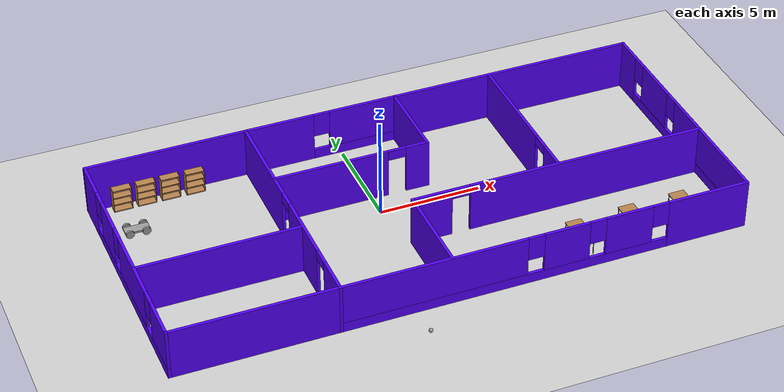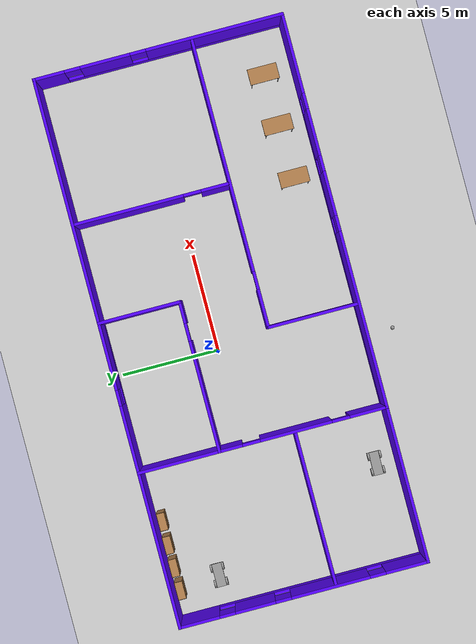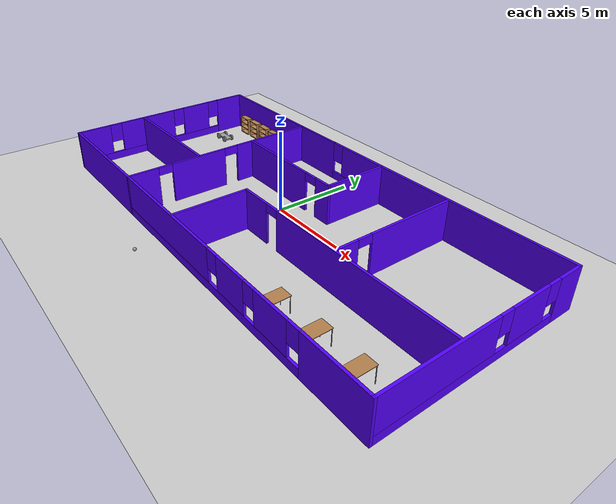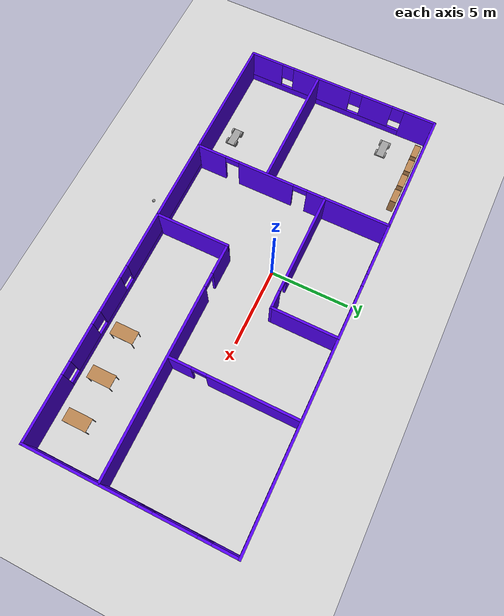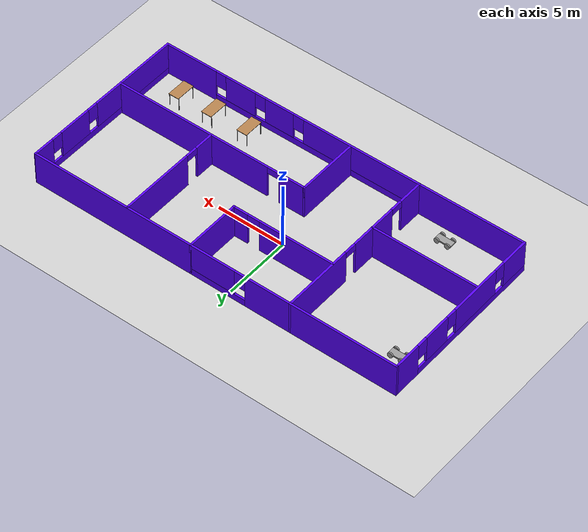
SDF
<sdf version="1.6">
 <world name="default">
  <plugin name="hello" filename="libhello.so"/>
  <light name="sun" type="directional">
   <pose>0 0 10 0 -0 0</pose>
   <diffuse>0.8 0.8 0.8 1</diffuse>
   <specular>0.2 0.2 0.2 1</specular>
   <attenuation>
    <range>1000</range>
    <constant>0.9</constant>
    <linear>0.01</linear>
    <quadratic>0.001</quadratic>
   </attenuation>
   <direction>-0.5 0.1 -0.9</direction>
  </light>
  <model name="ground_plane">
   <static>1</static>
   <link name="link">
    <collision name="collision">
     <geometry><plane><normal>0 0 1</normal><size>100 100</size></plane></geometry>
     <surface>
      <contact><collide_bitmask>65535</collide_bitmask></contact>
      <friction><ode><mu>100</mu><mu2>50</mu2></ode></friction>
     </surface>
    </collision>
    <visual name="visual">
     <cast_shadows>0</cast_shadows>
     <geometry><plane><normal>0 0 1</normal><size>100 100</size></plane></geometry>
     <material>
      <script><uri>file://media/materials/scripts/gazebo.material</uri><name>Gazebo/Grey</name></script>
     </material>
    </visual>
   </link>
  </model>
  <gravity>0 0 -9.8</gravity>
  <magnetic_field>6e-06 2.3e-05 -4.2e-05</magnetic_field>
  <atmosphere type="adiabatic"/>
  <physics name="default_physics" default="0" type="ode">
   <max_step_size>0.001</max_step_size>
   <real_time_factor>1</real_time_factor>
   <real_time_update_rate>1000</real_time_update_rate>
  </physics>
  <scene><ambient>0.4 0.4 0.4 1</ambient><background>0.7 0.7 0.7 1</background><shadows>1</shadows></scene>
  <spherical_coordinates>
   <surface_model>EARTH_WGS84</surface_model>
   <latitude_deg>0</latitude_deg>
   <longitude_deg>0</longitude_deg>
   <elevation>0</elevation>
   <heading_deg>0</heading_deg>
  </spherical_coordinates>
  <model name="mybuilding">
   <pose>1.28184 -1.00134 0 0 -0 0</pose>
   <link name="Wall_10">
    <collision name="Wall_10_Collision">
     <geometry><box><size>4.25 0.15 2.5</size></box></geometry>
     <pose>0 0 1.25 0 -0 0</pose>
    </collision>
    <visual name="Wall_10_Visual">
     <pose>0 0 1.25 0 -0 0</pose>
     <geometry><box><size>4.25 0.15 2.5</size></box></geometry>
     <material>
      <script><uri>file://media/materials/scripts/gazebo.material</uri><name>Gazebo/Grey</name></script>
      <ambient>0.333333 0 1 1</ambient>
     </material>
     <meta><layer>0</layer></meta>
    </visual>
    <pose>1.55 4.25 0 0 0 -1.5708</pose>
   </link>
   <link name="Wall_11">
    <pose>-2.25 2.2 0 0 -0 3.14159</pose>
    <visual name="Wall_11_Visual_0">
     <pose>-3.29403 0 1.25 0 -0 0</pose>
     <geometry><box><size>1.16194 0.15 2.5</size></box></geometry>
     <material>
      <script><uri>file://media/materials/scripts/gazebo.material</uri><name>Gazebo/Grey</name></script>
      <ambient>0.333333 0 1 1</ambient>
     </material>
     <meta><layer>0</layer></meta>
    </visual>
    <collision name="Wall_11_Collision_0">
     <geometry><box><size>1.16194 0.15 2.5</size></box></geometry>
     <pose>-3.29403 0 1.25 0 -0 0</pose>
    </collision>
    <visual name="Wall_11_Visual_1">
     <pose>1.03097 0 1.25 0 -0 0</pose>
     <geometry><box><size>5.68806 0.15 2.5</size></box></geometry>
     <material>
      <script><uri>file://media/materials/scripts/gazebo.material</uri><name>Gazebo/Grey</name></script>
      <ambient>0.333333 0 1 1</ambient>
     </material>
     <meta><layer>0</layer></meta>
    </visual>
    <collision name="Wall_11_Collision_1">
     <geometry><box><size>5.68806 0.15 2.5</size></box></geometry>
     <pose>1.03097 0 1.25 0 -0 0</pose>
    </collision>
    <visual name="Wall_11_Visual_2">
     <pose>-2.26306 0 2.25 0 -0 0</pose>
     <geometry><box><size>0.9 0.15 0.5</size></box></geometry>
     <material>
      <script><uri>file://media/materials/scripts/gazebo.material</uri><name>Gazebo/Grey</name></script>
      <ambient>0.333333 0 1 1</ambient>
     </material>
     <meta><layer>0</layer></meta>
    </visual>
    <collision name="Wall_11_Collision_2">
     <geometry><box><size>0.9 0.15 0.5</size></box></geometry>
     <pose>-2.26306 0 2.25 0 -0 0</pose>
    </collision>
   </link>
   <link name="Wall_13">
    <collision name="Wall_13_Collision">
     <geometry><box><size>12.5 0.15 2.5</size></box></geometry>
     <pose>0 0 1.25 0 -0 0</pose>
    </collision>
    <visual name="Wall_13_Visual">
     <pose>0 0 1.25 0 -0 0</pose>
     <geometry><box><size>12.5 0.15 2.5</size></box></geometry>
     <material>
      <script><uri>file://media/materials/scripts/gazebo.material</uri><name>Gazebo/Grey</name></script>
      <ambient>0.333333 0 1 1</ambient>
     </material>
     <meta><layer>0</layer></meta>
    </visual>
    <pose>7.725 6.3 0 0 -0 0</pose>
   </link>
   <link name="Wall_14">
    <pose>13.9 0 0 0 0 -1.5708</pose>
    <visual name="Wall_14_Visual_0">
     <pose>-5.56601 0 1.25 0 -0 0</pose>
     <geometry><box><size>1.61797 0.15 2.5</size></box></geometry>
     <material>
      <script><uri>file://media/materials/scripts/gazebo.material</uri><name>Gazebo/Grey</name></script>
      <ambient>0.333333 0 1 1</ambient>
     </material>
     <meta><layer>0</layer></meta>
    </visual>
    <collision name="Wall_14_Collision_0">
     <geometry><box><size>1.61797 0.15 2.5</size></box></geometry>
     <pose>-5.56601 0 1.25 0 -0 0</pose>
    </collision>
    <visual name="Wall_14_Visual_1">
     <pose>0.808986 0 0.25 0 -0 0</pose>
     <geometry><box><size>11.132 0.15 0.5</size></box></geometry>
     <material>
      <script><uri>file://media/materials/scripts/gazebo.material</uri><name>Gazebo/Grey</name></script>
      <ambient>0.333333 0 1 1</ambient>
     </material>
     <meta><layer>0</layer></meta>
    </visual>
    <collision name="Wall_14_Collision_1">
     <geometry><box><size>11.132 0.15 0.5</size></box></geometry>
     <pose>0.808986 0 0.25 0 -0 0</pose>
    </collision>
    <visual name="Wall_14_Visual_2">
     <pose>-2.69163 0 1.5 0 -0 0</pose>
     <geometry><box><size>2.53081 0.15 2</size></box></geometry>
     <material>
      <script><uri>file://media/materials/scripts/gazebo.material</uri><name>Gazebo/Grey</name></script>
      <ambient>0.333333 0 1 1</ambient>
     </material>
     <meta><layer>0</layer></meta>
    </visual>
    <collision name="Wall_14_Collision_2">
     <geometry><box><size>2.53081 0.15 2</size></box></geometry>
     <pose>-2.69163 0 1.5 0 -0 0</pose>
    </collision>
    <visual name="Wall_14_Visual_3">
     <pose>2.87439 0 1.5 0 -0 0</pose>
     <geometry><box><size>7.00122 0.15 2</size></box></geometry>
     <material>
      <script><uri>file://media/materials/scripts/gazebo.material</uri><name>Gazebo/Grey</name></script>
      <ambient>0.333333 0 1 1</ambient>
     </material>
     <meta><layer>0</layer></meta>
    </visual>
    <collision name="Wall_14_Collision_3">
     <geometry><box><size>7.00122 0.15 2</size></box></geometry>
     <pose>2.87439 0 1.5 0 -0 0</pose>
    </collision>
    <visual name="Wall_14_Visual_4">
     <pose>-4.35703 0 1.9 0 -0 0</pose>
     <geometry><box><size>0.8 0.15 1.2</size></box></geometry>
     <material>
      <script><uri>file://media/materials/scripts/gazebo.material</uri><name>Gazebo/Grey</name></script>
      <ambient>0.333333 0 1 1</ambient>
     </material>
     <meta><layer>0</layer></meta>
    </visual>
    <collision name="Wall_14_Collision_4">
     <geometry><box><size>0.8 0.15 1.2</size></box></geometry>
     <pose>-4.35703 0 1.9 0 -0 0</pose>
    </collision>
    <visual name="Wall_14_Visual_5">
     <pose>-1.02622 0 1.9 0 -0 0</pose>
     <geometry><box><size>0.8 0.15 1.2</size></box></geometry>
     <material>
      <script><uri>file://media/materials/scripts/gazebo.material</uri><name>Gazebo/Grey</name></script>
      <ambient>0.333333 0 1 1</ambient>
     </material>
     <meta><layer>0</layer></meta>
    </visual>
    <collision name="Wall_14_Collision_5">
     <geometry><box><size>0.8 0.15 1.2</size></box></geometry>
     <pose>-1.02622 0 1.9 0 -0 0</pose>
    </collision>
   </link>
   <link name="Wall_15">
    <pose>3.925 -6.3 0 0 -0 3.14159</pose>
    <visual name="Wall_15_Visual_0">
     <pose>-8.00502 0 1.25 0 -0 0</pose>
     <geometry><box><size>4.08996 0.15 2.5</size></box></geometry>
     <material>
      <script><uri>file://media/materials/scripts/gazebo.material</uri><name>Gazebo/Grey</name></script>
      <ambient>0.333333 0 1 1</ambient>
     </material>
     <meta><layer>0</layer></meta>
    </visual>
    <collision name="Wall_15_Collision_0">
     <geometry><box><size>4.08996 0.15 2.5</size></box></geometry>
     <pose>-8.00502 0 1.25 0 -0 0</pose>
    </collision>
    <visual name="Wall_15_Visual_1">
     <pose>2.04498 0 0.25 0 -0 0</pose>
     <geometry><box><size>16.01 0.15 0.5</size></box></geometry>
     <material>
      <script><uri>file://media/materials/scripts/gazebo.material</uri><name>Gazebo/Grey</name></script>
      <ambient>0.333333 0 1 1</ambient>
     </material>
     <meta><layer>0</layer></meta>
    </visual>
    <collision name="Wall_15_Collision_1">
     <geometry><box><size>16.01 0.15 0.5</size></box></geometry>
     <pose>2.04498 0 0.25 0 -0 0</pose>
    </collision>
    <visual name="Wall_15_Visual_2">
     <pose>-3.98138 0 1.5 0 -0 0</pose>
     <geometry><box><size>2.35733 0.15 2</size></box></geometry>
     <material>
      <script><uri>file://media/materials/scripts/gazebo.material</uri><name>Gazebo/Grey</name></script>
      <ambient>0.333333 0 1 1</ambient>
     </material>
     <meta><layer>0</layer></meta>
    </visual>
    <collision name="Wall_15_Collision_2">
     <geometry><box><size>2.35733 0.15 2</size></box></geometry>
     <pose>-3.98138 0 1.5 0 -0 0</pose>
    </collision>
    <visual name="Wall_15_Visual_3">
     <pose>-0.876096 0 1.5 0 -0 0</pose>
     <geometry><box><size>2.25324 0.15 2</size></box></geometry>
     <material>
      <script><uri>file://media/materials/scripts/gazebo.material</uri><name>Gazebo/Grey</name></script>
      <ambient>0.333333 0 1 1</ambient>
     </material>
     <meta><layer>0</layer></meta>
    </visual>
    <collision name="Wall_15_Collision_3">
     <geometry><box><size>2.25324 0.15 2</size></box></geometry>
     <pose>-0.876096 0 1.5 0 -0 0</pose>
    </collision>
    <visual name="Wall_15_Visual_4">
     <pose>5.55026 0 1.5 0 -0 0</pose>
     <geometry><box><size>8.99948 0.15 2</size></box></geometry>
     <material>
      <script><uri>file://media/materials/scripts/gazebo.material</uri><name>Gazebo/Grey</name></script>
      <ambient>0.333333 0 1 1</ambient>
     </material>
     <meta><layer>0</layer></meta>
    </visual>
    <collision name="Wall_15_Collision_4">
     <geometry><box><size>8.99948 0.15 2</size></box></geometry>
     <pose>5.55026 0 1.5 0 -0 0</pose>
    </collision>
    <visual name="Wall_15_Visual_5">
     <pose>-5.56004 0 1.9 0 -0 0</pose>
     <geometry><box><size>0.8 0.15 1.2</size></box></geometry>
     <material>
      <script><uri>file://media/materials/scripts/gazebo.material</uri><name>Gazebo/Grey</name></script>
      <ambient>0.333333 0 1 1</ambient>
     </material>
     <meta><layer>0</layer></meta>
    </visual>
    <collision name="Wall_15_Collision_5">
     <geometry><box><size>0.8 0.15 1.2</size></box></geometry>
     <pose>-5.56004 0 1.9 0 -0 0</pose>
    </collision>
    <visual name="Wall_15_Visual_6">
     <pose>-2.40272 0 1.9 0 -0 0</pose>
     <geometry><box><size>0.8 0.15 1.2</size></box></geometry>
     <material>
      <script><uri>file://media/materials/scripts/gazebo.material</uri><name>Gazebo/Grey</name></script>
      <ambient>0.333333 0 1 1</ambient>
     </material>
     <meta><layer>0</layer></meta>
    </visual>
    <collision name="Wall_15_Collision_6">
     <geometry><box><size>0.8 0.15 1.2</size></box></geometry>
     <pose>-2.40272 0 1.9 0 -0 0</pose>
    </collision>
    <visual name="Wall_15_Visual_7">
     <pose>0.650524 0 1.9 0 -0 0</pose>
     <geometry><box><size>0.8 0.15 1.2</size></box></geometry>
     <material>
      <script><uri>file://media/materials/scripts/gazebo.material</uri><name>Gazebo/Grey</name></script>
      <ambient>0.333333 0 1 1</ambient>
     </material>
     <meta><layer>0</layer></meta>
    </visual>
    <collision name="Wall_15_Collision_7">
     <geometry><box><size>0.8 0.15 1.2</size></box></geometry>
     <pose>0.650524 0 1.9 0 -0 0</pose>
    </collision>
   </link>
   <link name="Wall_17">
    <collision name="Wall_17_Collision">
     <geometry><box><size>4.75 0.15 2.5</size></box></geometry>
     <pose>0 0 1.25 0 -0 0</pose>
    </collision>
    <visual name="Wall_17_Visual">
     <pose>0 0 1.25 0 -0 0</pose>
     <geometry><box><size>4.75 0.15 2.5</size></box></geometry>
     <material>
      <script><uri>file://media/materials/scripts/gazebo.material</uri><name>Gazebo/Grey</name></script>
      <ambient>0.333333 0 1 1</ambient>
     </material>
     <meta><layer>0</layer></meta>
    </visual>
    <pose>-0.784945 -3.99462 0 0 -0 1.5708</pose>
   </link>
   <link name="Wall_18">
    <pose>6.51506 -1.69462 0 0 -0 0</pose>
    <visual name="Wall_18_Visual_0">
     <pose>-6.36549 0 1.25 0 -0 0</pose>
     <geometry><box><size>2.01902 0.15 2.5</size></box></geometry>
     <material>
      <script><uri>file://media/materials/scripts/gazebo.material</uri><name>Gazebo/Grey</name></script>
      <ambient>0.333333 0 1 1</ambient>
     </material>
     <meta><layer>0</layer></meta>
    </visual>
    <collision name="Wall_18_Collision_0">
     <geometry><box><size>2.01902 0.15 2.5</size></box></geometry>
     <pose>-6.36549 0 1.25 0 -0 0</pose>
    </collision>
    <visual name="Wall_18_Visual_1">
     <pose>1.45951 0 1.25 0 -0 0</pose>
     <geometry><box><size>11.831 0.15 2.5</size></box></geometry>
     <material>
      <script><uri>file://media/materials/scripts/gazebo.material</uri><name>Gazebo/Grey</name></script>
      <ambient>0.333333 0 1 1</ambient>
     </material>
     <meta><layer>0</layer></meta>
    </visual>
    <collision name="Wall_18_Collision_1">
     <geometry><box><size>11.831 0.15 2.5</size></box></geometry>
     <pose>1.45951 0 1.25 0 -0 0</pose>
    </collision>
    <visual name="Wall_18_Visual_2">
     <pose>-4.90598 0 2.25 0 -0 0</pose>
     <geometry><box><size>0.9 0.15 0.5</size></box></geometry>
     <material>
      <script><uri>file://media/materials/scripts/gazebo.material</uri><name>Gazebo/Grey</name></script>
      <ambient>0.333333 0 1 1</ambient>
     </material>
     <meta><layer>0</layer></meta>
    </visual>
    <collision name="Wall_18_Collision_2">
     <geometry><box><size>0.9 0.15 0.5</size></box></geometry>
     <pose>-4.90598 0 2.25 0 -0 0</pose>
    </collision>
   </link>
   <link name="Wall_2">
    <pose>-13.9 0 0 0 0 -1.5708</pose>
    <visual name="Wall_2_Visual_0">
     <pose>-5.32314 0 1.25 0 -0 0</pose>
     <geometry><box><size>2.10371 0.15 2.5</size></box></geometry>
     <material>
      <script><uri>file://media/materials/scripts/gazebo.material</uri><name>Gazebo/Grey</name></script>
      <ambient>0.333333 0 1 1</ambient>
     </material>
     <meta><layer>0</layer></meta>
    </visual>
    <collision name="Wall_2_Collision_0">
     <geometry><box><size>2.10371 0.15 2.5</size></box></geometry>
     <pose>-5.32314 0 1.25 0 -0 0</pose>
    </collision>
    <visual name="Wall_2_Visual_1">
     <pose>1.05186 0 0.25 0 -0 0</pose>
     <geometry><box><size>10.6463 0.15 0.5</size></box></geometry>
     <material>
      <script><uri>file://media/materials/scripts/gazebo.material</uri><name>Gazebo/Grey</name></script>
      <ambient>0.333333 0 1 1</ambient>
     </material>
     <meta><layer>0</layer></meta>
    </visual>
    <collision name="Wall_2_Collision_1">
     <geometry><box><size>10.6463 0.15 0.5</size></box></geometry>
     <pose>1.05186 0 0.25 0 -0 0</pose>
    </collision>
    <visual name="Wall_2_Visual_2">
     <pose>-2.44875 0 1.5 0 -0 0</pose>
     <geometry><box><size>2.04506 0.15 2</size></box></geometry>
     <material>
      <script><uri>file://media/materials/scripts/gazebo.material</uri><name>Gazebo/Grey</name></script>
      <ambient>0.333333 0 1 1</ambient>
     </material>
     <meta><layer>0</layer></meta>
    </visual>
    <collision name="Wall_2_Collision_2">
     <geometry><box><size>2.04506 0.15 2</size></box></geometry>
     <pose>-2.44875 0 1.5 0 -0 0</pose>
    </collision>
    <visual name="Wall_2_Visual_3">
     <pose>1.3678 0 1.5 0 -0 0</pose>
     <geometry><box><size>3.98804 0.15 2</size></box></geometry>
     <material>
      <script><uri>file://media/materials/scripts/gazebo.material</uri><name>Gazebo/Grey</name></script>
      <ambient>0.333333 0 1 1</ambient>
     </material>
     <meta><layer>0</layer></meta>
    </visual>
    <collision name="Wall_2_Collision_3">
     <geometry><box><size>3.98804 0.15 2</size></box></geometry>
     <pose>1.3678 0 1.5 0 -0 0</pose>
    </collision>
    <visual name="Wall_2_Visual_4">
     <pose>5.26841 0 1.5 0 -0 0</pose>
     <geometry><box><size>2.21319 0.15 2</size></box></geometry>
     <material>
      <script><uri>file://media/materials/scripts/gazebo.material</uri><name>Gazebo/Grey</name></script>
      <ambient>0.333333 0 1 1</ambient>
     </material>
     <meta><layer>0</layer></meta>
    </visual>
    <collision name="Wall_2_Collision_4">
     <geometry><box><size>2.21319 0.15 2</size></box></geometry>
     <pose>5.26841 0 1.5 0 -0 0</pose>
    </collision>
    <visual name="Wall_2_Visual_5">
     <pose>-3.87129 0 1.9 0 -0 0</pose>
     <geometry><box><size>0.8 0.15 1.2</size></box></geometry>
     <material>
      <script><uri>file://media/materials/scripts/gazebo.material</uri><name>Gazebo/Grey</name></script>
      <ambient>0.333333 0 1 1</ambient>
     </material>
     <meta><layer>0</layer></meta>
    </visual>
    <collision name="Wall_2_Collision_5">
     <geometry><box><size>0.8 0.15 1.2</size></box></geometry>
     <pose>-3.87129 0 1.9 0 -0 0</pose>
    </collision>
    <visual name="Wall_2_Visual_6">
     <pose>-1.02622 0 1.9 0 -0 0</pose>
     <geometry><box><size>0.8 0.15 1.2</size></box></geometry>
     <material>
      <script><uri>file://media/materials/scripts/gazebo.material</uri><name>Gazebo/Grey</name></script>
      <ambient>0.333333 0 1 1</ambient>
     </material>
     <meta><layer>0</layer></meta>
    </visual>
    <collision name="Wall_2_Collision_6">
     <geometry><box><size>0.8 0.15 1.2</size></box></geometry>
     <pose>-1.02622 0 1.9 0 -0 0</pose>
    </collision>
    <visual name="Wall_2_Visual_7">
     <pose>3.76181 0 1.9 0 -0 0</pose>
     <geometry><box><size>0.8 0.15 1.2</size></box></geometry>
     <material>
      <script><uri>file://media/materials/scripts/gazebo.material</uri><name>Gazebo/Grey</name></script>
      <ambient>0.333333 0 1 1</ambient>
     </material>
     <meta><layer>0</layer></meta>
    </visual>
    <collision name="Wall_2_Collision_7">
     <geometry><box><size>0.8 0.15 1.2</size></box></geometry>
     <pose>3.76181 0 1.9 0 -0 0</pose>
    </collision>
   </link>
   <link name="Wall_22">
    <pose>6.53589 2.3403 0 0 0 -1.5708</pose>
    <visual name="Wall_22_Visual_0">
     <pose>-1.16896 0 1.25 0 -0 0</pose>
     <geometry><box><size>5.66209 0.15 2.5</size></box></geometry>
     <material>
      <script><uri>file://media/materials/scripts/gazebo.material</uri><name>Gazebo/Grey</name></script>
      <ambient>0.333333 0 1 1</ambient>
     </material>
     <meta><layer>0</layer></meta>
    </visual>
    <collision name="Wall_22_Collision_0">
     <geometry><box><size>5.66209 0.15 2.5</size></box></geometry>
     <pose>-1.16896 0 1.25 0 -0 0</pose>
    </collision>
    <visual name="Wall_22_Visual_1">
     <pose>3.28104 0 1.25 0 -0 0</pose>
     <geometry><box><size>1.43791 0.15 2.5</size></box></geometry>
     <material>
      <script><uri>file://media/materials/scripts/gazebo.material</uri><name>Gazebo/Grey</name></script>
      <ambient>0.333333 0 1 1</ambient>
     </material>
     <meta><layer>0</layer></meta>
    </visual>
    <collision name="Wall_22_Collision_1">
     <geometry><box><size>1.43791 0.15 2.5</size></box></geometry>
     <pose>3.28104 0 1.25 0 -0 0</pose>
    </collision>
    <visual name="Wall_22_Visual_2">
     <pose>2.11209 0 2.25 0 -0 0</pose>
     <geometry><box><size>0.9 0.15 0.5</size></box></geometry>
     <material>
      <script><uri>file://media/materials/scripts/gazebo.material</uri><name>Gazebo/Grey</name></script>
      <ambient>0.333333 0 1 1</ambient>
     </material>
     <meta><layer>0</layer></meta>
    </visual>
    <collision name="Wall_22_Collision_2">
     <geometry><box><size>0.9 0.15 0.5</size></box></geometry>
     <pose>2.11209 0 2.25 0 -0 0</pose>
    </collision>
   </link>
   <link name="Wall_3">
    <collision name="Wall_3_Collision">
     <geometry><box><size>8 0.15 2.5</size></box></geometry>
     <pose>0 0 1.25 0 -0 0</pose>
    </collision>
    <visual name="Wall_3_Visual">
     <pose>0 0 1.25 0 -0 0</pose>
     <geometry><box><size>8 0.15 2.5</size></box></geometry>
     <material>
      <script><uri>file://media/materials/scripts/gazebo.material</uri><name>Gazebo/Grey</name></script>
      <ambient>0.333333 0 1 1</ambient>
     </material>
     <meta><layer>0</layer></meta>
    </visual>
    <pose>-9.975 -6.3 0 0 -0 0</pose>
   </link>
   <link name="Wall_4">
    <pose>-6.05 0 0 0 -0 1.5708</pose>
    <visual name="Wall_4_Visual_0">
     <pose>-5.3975 0 1.25 0 -0 0</pose>
     <geometry><box><size>1.95501 0.15 2.5</size></box></geometry>
     <material>
      <script><uri>file://media/materials/scripts/gazebo.material</uri><name>Gazebo/Grey</name></script>
      <ambient>0.333333 0 1 1</ambient>
     </material>
     <meta><layer>0</layer></meta>
    </visual>
    <collision name="Wall_4_Collision_0">
     <geometry><box><size>1.95501 0.15 2.5</size></box></geometry>
     <pose>-5.3975 0 1.25 0 -0 0</pose>
    </collision>
    <visual name="Wall_4_Visual_1">
     <pose>-1.69741 0 1.25 0 -0 0</pose>
     <geometry><box><size>3.64516 0.15 2.5</size></box></geometry>
     <material>
      <script><uri>file://media/materials/scripts/gazebo.material</uri><name>Gazebo/Grey</name></script>
      <ambient>0.333333 0 1 1</ambient>
     </material>
     <meta><layer>0</layer></meta>
    </visual>
    <collision name="Wall_4_Collision_1">
     <geometry><box><size>3.64516 0.15 2.5</size></box></geometry>
     <pose>-1.69741 0 1.25 0 -0 0</pose>
    </collision>
    <visual name="Wall_4_Visual_2">
     <pose>3.70009 0 1.25 0 -0 0</pose>
     <geometry><box><size>5.34983 0.15 2.5</size></box></geometry>
     <material>
      <script><uri>file://media/materials/scripts/gazebo.material</uri><name>Gazebo/Grey</name></script>
      <ambient>0.333333 0 1 1</ambient>
     </material>
     <meta><layer>0</layer></meta>
    </visual>
    <collision name="Wall_4_Collision_2">
     <geometry><box><size>5.34983 0.15 2.5</size></box></geometry>
     <pose>3.70009 0 1.25 0 -0 0</pose>
    </collision>
    <visual name="Wall_4_Visual_3">
     <pose>-3.96999 0 2.25 0 -0 0</pose>
     <geometry><box><size>0.9 0.15 0.5</size></box></geometry>
     <material>
      <script><uri>file://media/materials/scripts/gazebo.material</uri><name>Gazebo/Grey</name></script>
      <ambient>0.333333 0 1 1</ambient>
     </material>
     <meta><layer>0</layer></meta>
    </visual>
    <collision name="Wall_4_Collision_3">
     <geometry><box><size>0.9 0.15 0.5</size></box></geometry>
     <pose>-3.96999 0 2.25 0 -0 0</pose>
    </collision>
    <visual name="Wall_4_Visual_4">
     <pose>0.575175 0 2.25 0 -0 0</pose>
     <geometry><box><size>0.9 0.15 0.5</size></box></geometry>
     <material>
      <script><uri>file://media/materials/scripts/gazebo.material</uri><name>Gazebo/Grey</name></script>
      <ambient>0.333333 0 1 1</ambient>
     </material>
     <meta><layer>0</layer></meta>
    </visual>
    <collision name="Wall_4_Collision_4">
     <geometry><box><size>0.9 0.15 0.5</size></box></geometry>
     <pose>0.575175 0 2.25 0 -0 0</pose>
    </collision>
   </link>
   <link name="Wall_5">
    <collision name="Wall_5_Collision">
     <geometry><box><size>8 0.15 2.5</size></box></geometry>
     <pose>0 0 1.25 0 -0 0</pose>
    </collision>
    <visual name="Wall_5_Visual">
     <pose>0 0 1.25 0 -0 0</pose>
     <geometry><box><size>8 0.15 2.5</size></box></geometry>
     <material>
      <script><uri>file://media/materials/scripts/gazebo.material</uri><name>Gazebo/Grey</name></script>
      <ambient>0.333333 0 1 1</ambient>
     </material>
     <meta><layer>0</layer></meta>
    </visual>
    <pose>-9.975 6.3 0 0 -0 3.14159</pose>
   </link>
   <link name="Wall_7">
    <collision name="Wall_7_Collision">
     <geometry><box><size>8 0.15 2.5</size></box></geometry>
     <pose>0 0 1.25 0 -0 0</pose>
    </collision>
    <visual name="Wall_7_Visual">
     <pose>0 0 1.25 0 -0 0</pose>
     <geometry><box><size>8 0.15 2.5</size></box></geometry>
     <material>
      <script><uri>file://media/materials/scripts/gazebo.material</uri><name>Gazebo/Grey</name></script>
      <ambient>0.333333 0 1 1</ambient>
     </material>
     <meta><layer>0</layer></meta>
    </visual>
    <pose>-9.975 -1.64536 0 0 -0 0</pose>
   </link>
   <link name="Wall_9">
    <pose>-2.25 6.3 0 0 -0 0</pose>
    <visual name="Wall_9_Visual_0">
     <pose>-2.13359 0 1.25 0 -0 0</pose>
     <geometry><box><size>3.48283 0.15 2.5</size></box></geometry>
     <material>
      <script><uri>file://media/materials/scripts/gazebo.material</uri><name>Gazebo/Grey</name></script>
      <ambient>0.333333 0 1 1</ambient>
     </material>
     <meta><layer>0</layer></meta>
    </visual>
    <collision name="Wall_9_Collision_0">
     <geometry><box><size>3.48283 0.15 2.5</size></box></geometry>
     <pose>-2.13359 0 1.25 0 -0 0</pose>
    </collision>
    <visual name="Wall_9_Visual_1">
     <pose>1.74141 0 0.25 0 -0 0</pose>
     <geometry><box><size>4.26717 0.15 0.5</size></box></geometry>
     <material>
      <script><uri>file://media/materials/scripts/gazebo.material</uri><name>Gazebo/Grey</name></script>
      <ambient>0.333333 0 1 1</ambient>
     </material>
     <meta><layer>0</layer></meta>
    </visual>
    <collision name="Wall_9_Collision_1">
     <geometry><box><size>4.26717 0.15 0.5</size></box></geometry>
     <pose>1.74141 0 0.25 0 -0 0</pose>
    </collision>
    <visual name="Wall_9_Visual_2">
     <pose>2.14141 0 1.5 0 -0 0</pose>
     <geometry><box><size>3.46717 0.15 2</size></box></geometry>
     <material>
      <script><uri>file://media/materials/scripts/gazebo.material</uri><name>Gazebo/Grey</name></script>
      <ambient>0.333333 0 1 1</ambient>
     </material>
     <meta><layer>0</layer></meta>
    </visual>
    <collision name="Wall_9_Collision_2">
     <geometry><box><size>3.46717 0.15 2</size></box></geometry>
     <pose>2.14141 0 1.5 0 -0 0</pose>
    </collision>
    <visual name="Wall_9_Visual_3">
     <pose>0.007826 0 1.9 0 -0 0</pose>
     <geometry><box><size>0.8 0.15 1.2</size></box></geometry>
     <material>
      <script><uri>file://media/materials/scripts/gazebo.material</uri><name>Gazebo/Grey</name></script>
      <ambient>0.333333 0 1 1</ambient>
     </material>
     <meta><layer>0</layer></meta>
    </visual>
    <collision name="Wall_9_Collision_3">
     <geometry><box><size>0.8 0.15 1.2</size></box></geometry>
     <pose>0.007826 0 1.9 0 -0 0</pose>
    </collision>
   </link>
   <static>1</static>
  </model>
  <model name="table">
   <static>1</static>
   <link name="link">
    <collision name="surface">
     <pose>0 0 1 0 -0 0</pose>
     <geometry><box><size>1.5 0.8 0.03</size></box></geometry>
     <surface><friction><ode><mu>0.6</mu><mu2>0.6</mu2></ode></friction></surface>
    </collision>
    <visual name="visual1">
     <pose>0 0 1 0 -0 0</pose>
     <geometry><box><size>1.5 0.8 0.03</size></box></geometry>
     <material>
      <script><uri>file://media/materials/scripts/gazebo.material</uri><name>Gazebo/Wood</name></script>
     </material>
    </visual>
    <collision name="front_left_leg">
     <pose>0.68 0.38 0.5 0 -0 0</pose>
     <geometry><cylinder><radius>0.02</radius><length>1</length></cylinder></geometry>
    </collision>
    <visual name="front_left_leg">
     <pose>0.68 0.38 0.5 0 -0 0</pose>
     <geometry><cylinder><radius>0.02</radius><length>1</length></cylinder></geometry>
     <material>
      <script><uri>file://media/materials/scripts/gazebo.material</uri><name>Gazebo/Grey</name></script>
     </material>
    </visual>
    <collision name="front_right_leg">
     <pose>0.68 -0.38 0.5 0 -0 0</pose>
     <geometry><cylinder><radius>0.02</radius><length>1</length></cylinder></geometry>
    </collision>
    <visual name="front_right_leg">
     <pose>0.68 -0.38 0.5 0 -0 0</pose>
     <geometry><cylinder><radius>0.02</radius><length>1</length></cylinder></geometry>
     <material>
      <script><uri>file://media/materials/scripts/gazebo.material</uri><name>Gazebo/Grey</name></script>
     </material>
    </visual>
    <collision name="back_right_leg">
     <pose>-0.68 -0.38 0.5 0 -0 0</pose>
     <geometry><cylinder><radius>0.02</radius><length>1</length></cylinder></geometry>
    </collision>
    <visual name="back_right_leg">
     <pose>-0.68 -0.38 0.5 0 -0 0</pose>
     <geometry><cylinder><radius>0.02</radius><length>1</length></cylinder></geometry>
     <material>
      <script><uri>file://media/materials/scripts/gazebo.material</uri><name>Gazebo/Grey</name></script>
     </material>
    </visual>
    <collision name="back_left_leg">
     <pose>-0.68 0.38 0.5 0 -0 0</pose>
     <geometry><cylinder><radius>0.02</radius><length>1</length></cylinder></geometry>
    </collision>
    <visual name="back_left_leg">
     <pose>-0.68 0.38 0.5 0 -0 0</pose>
     <geometry><cylinder><radius>0.02</radius><length>1</length></cylinder></geometry>
     <material>
      <script><uri>file://media/materials/scripts/gazebo.material</uri><name>Gazebo/Grey</name></script>
     </material>
    </visual>
   </link>
   <pose>7.43515 -5.90461 0 0 -0 1.57</pose>
  </model>
  <model name="table_clone">
   <static>1</static>
   <link name="link">
    <collision name="surface">
     <pose>0 0 1 0 -0 0</pose>
     <geometry><box><size>1.5 0.8 0.03</size></box></geometry>
     <surface><friction><ode><mu>0.6</mu><mu2>0.6</mu2></ode></friction></surface>
    </collision>
    <visual name="visual1">
     <pose>0 0 1 0 -0 0</pose>
     <geometry><box><size>1.5 0.8 0.03</size></box></geometry>
     <material>
      <script><uri>file://media/materials/scripts/gazebo.material</uri><name>Gazebo/Wood</name></script>
     </material>
    </visual>
    <collision name="front_left_leg">
     <pose>0.68 0.38 0.5 0 -0 0</pose>
     <geometry><cylinder><radius>0.02</radius><length>1</length></cylinder></geometry>
    </collision>
    <visual name="front_left_leg">
     <pose>0.68 0.38 0.5 0 -0 0</pose>
     <geometry><cylinder><radius>0.02</radius><length>1</length></cylinder></geometry>
     <material>
      <script><uri>file://media/materials/scripts/gazebo.material</uri><name>Gazebo/Grey</name></script>
     </material>
    </visual>
    <collision name="front_right_leg">
     <pose>0.68 -0.38 0.5 0 -0 0</pose>
     <geometry><cylinder><radius>0.02</radius><length>1</length></cylinder></geometry>
    </collision>
    <visual name="front_right_leg">
     <pose>0.68 -0.38 0.5 0 -0 0</pose>
     <geometry><cylinder><radius>0.02</radius><length>1</length></cylinder></geometry>
     <material>
      <script><uri>file://media/materials/scripts/gazebo.material</uri><name>Gazebo/Grey</name></script>
     </material>
    </visual>
    <collision name="back_right_leg">
     <pose>-0.68 -0.38 0.5 0 -0 0</pose>
     <geometry><cylinder><radius>0.02</radius><length>1</length></cylinder></geometry>
    </collision>
    <visual name="back_right_leg">
     <pose>-0.68 -0.38 0.5 0 -0 0</pose>
     <geometry><cylinder><radius>0.02</radius><length>1</length></cylinder></geometry>
     <material>
      <script><uri>file://media/materials/scripts/gazebo.material</uri><name>Gazebo/Grey</name></script>
     </material>
    </visual>
    <collision name="back_left_leg">
     <pose>-0.68 0.38 0.5 0 -0 0</pose>
     <geometry><cylinder><radius>0.02</radius><length>1</length></cylinder></geometry>
    </collision>
    <visual name="back_left_leg">
     <pose>-0.68 0.38 0.5 0 -0 0</pose>
     <geometry><cylinder><radius>0.02</radius><length>1</length></cylinder></geometry>
     <material>
      <script><uri>file://media/materials/scripts/gazebo.material</uri><name>Gazebo/Grey</name></script>
     </material>
    </visual>
   </link>
   <pose>10.1933 -5.79065 0 0 -0 1.57</pose>
  </model>
  <model name="table_clone_clone">
   <static>1</static>
   <link name="link">
    <collision name="surface">
     <pose>0 0 1 0 -0 0</pose>
     <geometry><box><size>1.5 0.8 0.03</size></box></geometry>
     <surface><friction><ode><mu>0.6</mu><mu2>0.6</mu2></ode></friction></surface>
    </collision>
    <visual name="visual1">
     <pose>0 0 1 0 -0 0</pose>
     <geometry><box><size>1.5 0.8 0.03</size></box></geometry>
     <material>
      <script><uri>file://media/materials/scripts/gazebo.material</uri><name>Gazebo/Wood</name></script>
     </material>
    </visual>
    <collision name="front_left_leg">
     <pose>0.68 0.38 0.5 0 -0 0</pose>
     <geometry><cylinder><radius>0.02</radius><length>1</length></cylinder></geometry>
    </collision>
    <visual name="front_left_leg">
     <pose>0.68 0.38 0.5 0 -0 0</pose>
     <geometry><cylinder><radius>0.02</radius><length>1</length></cylinder></geometry>
     <material>
      <script><uri>file://media/materials/scripts/gazebo.material</uri><name>Gazebo/Grey</name></script>
     </material>
    </visual>
    <collision name="front_right_leg">
     <pose>0.68 -0.38 0.5 0 -0 0</pose>
     <geometry><cylinder><radius>0.02</radius><length>1</length></cylinder></geometry>
    </collision>
    <visual name="front_right_leg">
     <pose>0.68 -0.38 0.5 0 -0 0</pose>
     <geometry><cylinder><radius>0.02</radius><length>1</length></cylinder></geometry>
     <material>
      <script><uri>file://media/materials/scripts/gazebo.material</uri><name>Gazebo/Grey</name></script>
     </material>
    </visual>
    <collision name="back_right_leg">
     <pose>-0.68 -0.38 0.5 0 -0 0</pose>
     <geometry><cylinder><radius>0.02</radius><length>1</length></cylinder></geometry>
    </collision>
    <visual name="back_right_leg">
     <pose>-0.68 -0.38 0.5 0 -0 0</pose>
     <geometry><cylinder><radius>0.02</radius><length>1</length></cylinder></geometry>
     <material>
      <script><uri>file://media/materials/scripts/gazebo.material</uri><name>Gazebo/Grey</name></script>
     </material>
    </visual>
    <collision name="back_left_leg">
     <pose>-0.68 0.38 0.5 0 -0 0</pose>
     <geometry><cylinder><radius>0.02</radius><length>1</length></cylinder></geometry>
    </collision>
    <visual name="back_left_leg">
     <pose>-0.68 0.38 0.5 0 -0 0</pose>
     <geometry><cylinder><radius>0.02</radius><length>1</length></cylinder></geometry>
     <material>
      <script><uri>file://media/materials/scripts/gazebo.material</uri><name>Gazebo/Grey</name></script>
     </material>
    </visual>
   </link>
   <pose>12.831 -5.75624 0 0 -0 1.57</pose>
  </model>
  <model name="bookshelf">
   <static>1</static>
   <link name="link">
    <inertial><mass>1</mass></inertial>
    <collision name="back">
     <pose>0 0.005 0.6 0 -0 0</pose>
     <geometry><box><size>0.9 0.01 1.2</size></box></geometry>
    </collision>
    <visual name="visual1">
     <pose>0 0.005 0.6 0 -0 0</pose>
     <geometry><box><size>0.9 0.01 1.2</size></box></geometry>
     <material>
      <script><uri>file://media/materials/scripts/gazebo.material</uri><name>Gazebo/Wood</name></script>
     </material>
    </visual>
    <collision name="left_side">
     <pose>0.45 -0.195 0.6 0 -0 0</pose>
     <geometry><box><size>0.02 0.4 1.2</size></box></geometry>
    </collision>
    <visual name="visual2">
     <pose>0.45 -0.195 0.6 0 -0 0</pose>
     <geometry><box><size>0.02 0.4 1.2</size></box></geometry>
     <material>
      <script><uri>file://media/materials/scripts/gazebo.material</uri><name>Gazebo/Wood</name></script>
     </material>
    </visual>
    <collision name="right_side">
     <pose>-0.45 -0.195 0.6 0 -0 0</pose>
     <geometry><box><size>0.02 0.4 1.2</size></box></geometry>
    </collision>
    <visual name="visual3">
     <pose>-0.45 -0.195 0.6 0 -0 0</pose>
     <geometry><box><size>0.02 0.4 1.2</size></box></geometry>
     <material>
      <script><uri>file://media/materials/scripts/gazebo.material</uri><name>Gazebo/Wood</name></script>
     </material>
    </visual>
    <collision name="bottom">
     <pose>0 -0.195 0.03 0 -0 0</pose>
     <geometry><box><size>0.88 0.4 0.06</size></box></geometry>
    </collision>
    <visual name="visual4">
     <pose>0 -0.195 0.03 0 -0 0</pose>
     <geometry><box><size>0.88 0.4 0.06</size></box></geometry>
     <material>
      <script><uri>file://media/materials/scripts/gazebo.material</uri><name>Gazebo/Wood</name></script>
     </material>
    </visual>
    <collision name="top">
     <pose>0 -0.195 1.19 0 -0 0</pose>
     <geometry><box><size>0.88 0.4 0.02</size></box></geometry>
    </collision>
    <visual name="visual5">
     <pose>0 -0.195 1.19 0 -0 0</pose>
     <geometry><box><size>0.88 0.4 0.02</size></box></geometry>
     <material>
      <script><uri>file://media/materials/scripts/gazebo.material</uri><name>Gazebo/Wood</name></script>
     </material>
    </visual>
    <collision name="low_shelf">
     <pose>0 -0.195 0.43 0 -0 0</pose>
     <geometry><box><size>0.88 0.4 0.02</size></box></geometry>
    </collision>
    <visual name="visual6">
     <pose>0 -0.195 0.43 0 -0 0</pose>
     <geometry><box><size>0.88 0.4 0.02</size></box></geometry>
     <material>
      <script><uri>file://media/materials/scripts/gazebo.material</uri><name>Gazebo/Wood</name></script>
     </material>
    </visual>
    <collision name="high_shelf">
     <pose>0 -0.195 0.8 0 -0 0</pose>
     <geometry><box><size>0.88 0.4 0.02</size></box></geometry>
    </collision>
    <visual name="visual7">
     <pose>0 -0.195 0.8 0 -0 0</pose>
     <geometry><box><size>0.88 0.4 0.02</size></box></geometry>
     <material>
      <script><uri>file://media/materials/scripts/gazebo.material</uri><name>Gazebo/Wood</name></script>
     </material>
    </visual>
   </link>
   <pose>-11.095 5.12258 0 0 -0 0</pose>
  </model>
  <model name="bookshelf_clone">
   <static>1</static>
   <link name="link">
    <inertial><mass>1</mass></inertial>
    <collision name="back">
     <pose>0 0.005 0.6 0 -0 0</pose>
     <geometry><box><size>0.9 0.01 1.2</size></box></geometry>
    </collision>
    <visual name="visual1">
     <pose>0 0.005 0.6 0 -0 0</pose>
     <geometry><box><size>0.9 0.01 1.2</size></box></geometry>
     <material>
      <script><uri>file://media/materials/scripts/gazebo.material</uri><name>Gazebo/Wood</name></script>
     </material>
    </visual>
    <collision name="left_side">
     <pose>0.45 -0.195 0.6 0 -0 0</pose>
     <geometry><box><size>0.02 0.4 1.2</size></box></geometry>
    </collision>
    <visual name="visual2">
     <pose>0.45 -0.195 0.6 0 -0 0</pose>
     <geometry><box><size>0.02 0.4 1.2</size></box></geometry>
     <material>
      <script><uri>file://media/materials/scripts/gazebo.material</uri><name>Gazebo/Wood</name></script>
     </material>
    </visual>
    <collision name="right_side">
     <pose>-0.45 -0.195 0.6 0 -0 0</pose>
     <geometry><box><size>0.02 0.4 1.2</size></box></geometry>
    </collision>
    <visual name="visual3">
     <pose>-0.45 -0.195 0.6 0 -0 0</pose>
     <geometry><box><size>0.02 0.4 1.2</size></box></geometry>
     <material>
      <script><uri>file://media/materials/scripts/gazebo.material</uri><name>Gazebo/Wood</name></script>
     </material>
    </visual>
    <collision name="bottom">
     <pose>0 -0.195 0.03 0 -0 0</pose>
     <geometry><box><size>0.88 0.4 0.06</size></box></geometry>
    </collision>
    <visual name="visual4">
     <pose>0 -0.195 0.03 0 -0 0</pose>
     <geometry><box><size>0.88 0.4 0.06</size></box></geometry>
     <material>
      <script><uri>file://media/materials/scripts/gazebo.material</uri><name>Gazebo/Wood</name></script>
     </material>
    </visual>
    <collision name="top">
     <pose>0 -0.195 1.19 0 -0 0</pose>
     <geometry><box><size>0.88 0.4 0.02</size></box></geometry>
    </collision>
    <visual name="visual5">
     <pose>0 -0.195 1.19 0 -0 0</pose>
     <geometry><box><size>0.88 0.4 0.02</size></box></geometry>
     <material>
      <script><uri>file://media/materials/scripts/gazebo.material</uri><name>Gazebo/Wood</name></script>
     </material>
    </visual>
    <collision name="low_shelf">
     <pose>0 -0.195 0.43 0 -0 0</pose>
     <geometry><box><size>0.88 0.4 0.02</size></box></geometry>
    </collision>
    <visual name="visual6">
     <pose>0 -0.195 0.43 0 -0 0</pose>
     <geometry><box><size>0.88 0.4 0.02</size></box></geometry>
     <material>
      <script><uri>file://media/materials/scripts/gazebo.material</uri><name>Gazebo/Wood</name></script>
     </material>
    </visual>
    <collision name="high_shelf">
     <pose>0 -0.195 0.8 0 -0 0</pose>
     <geometry><box><size>0.88 0.4 0.02</size></box></geometry>
    </collision>
    <visual name="visual7">
     <pose>0 -0.195 0.8 0 -0 0</pose>
     <geometry><box><size>0.88 0.4 0.02</size></box></geometry>
     <material>
      <script><uri>file://media/materials/scripts/gazebo.material</uri><name>Gazebo/Wood</name></script>
     </material>
    </visual>
   </link>
   <pose>-9.92346 5.1367 0 0 -0 0</pose>
  </model>
  <model name="bookshelf_clone_0">
   <static>1</static>
   <link name="link">
    <inertial><mass>1</mass></inertial>
    <collision name="back">
     <pose>0 0.005 0.6 0 -0 0</pose>
     <geometry><box><size>0.9 0.01 1.2</size></box></geometry>
    </collision>
    <visual name="visual1">
     <pose>0 0.005 0.6 0 -0 0</pose>
     <geometry><box><size>0.9 0.01 1.2</size></box></geometry>
     <material>
      <script><uri>file://media/materials/scripts/gazebo.material</uri><name>Gazebo/Wood</name></script>
     </material>
    </visual>
    <collision name="left_side">
     <pose>0.45 -0.195 0.6 0 -0 0</pose>
     <geometry><box><size>0.02 0.4 1.2</size></box></geometry>
    </collision>
    <visual name="visual2">
     <pose>0.45 -0.195 0.6 0 -0 0</pose>
     <geometry><box><size>0.02 0.4 1.2</size></box></geometry>
     <material>
      <script><uri>file://media/materials/scripts/gazebo.material</uri><name>Gazebo/Wood</name></script>
     </material>
    </visual>
    <collision name="right_side">
     <pose>-0.45 -0.195 0.6 0 -0 0</pose>
     <geometry><box><size>0.02 0.4 1.2</size></box></geometry>
    </collision>
    <visual name="visual3">
     <pose>-0.45 -0.195 0.6 0 -0 0</pose>
     <geometry><box><size>0.02 0.4 1.2</size></box></geometry>
     <material>
      <script><uri>file://media/materials/scripts/gazebo.material</uri><name>Gazebo/Wood</name></script>
     </material>
    </visual>
    <collision name="bottom">
     <pose>0 -0.195 0.03 0 -0 0</pose>
     <geometry><box><size>0.88 0.4 0.06</size></box></geometry>
    </collision>
    <visual name="visual4">
     <pose>0 -0.195 0.03 0 -0 0</pose>
     <geometry><box><size>0.88 0.4 0.06</size></box></geometry>
     <material>
      <script><uri>file://media/materials/scripts/gazebo.material</uri><name>Gazebo/Wood</name></script>
     </material>
    </visual>
    <collision name="top">
     <pose>0 -0.195 1.19 0 -0 0</pose>
     <geometry><box><size>0.88 0.4 0.02</size></box></geometry>
    </collision>
    <visual name="visual5">
     <pose>0 -0.195 1.19 0 -0 0</pose>
     <geometry><box><size>0.88 0.4 0.02</size></box></geometry>
     <material>
      <script><uri>file://media/materials/scripts/gazebo.material</uri><name>Gazebo/Wood</name></script>
     </material>
    </visual>
    <collision name="low_shelf">
     <pose>0 -0.195 0.43 0 -0 0</pose>
     <geometry><box><size>0.88 0.4 0.02</size></box></geometry>
    </collision>
    <visual name="visual6">
     <pose>0 -0.195 0.43 0 -0 0</pose>
     <geometry><box><size>0.88 0.4 0.02</size></box></geometry>
     <material>
      <script><uri>file://media/materials/scripts/gazebo.material</uri><name>Gazebo/Wood</name></script>
     </material>
    </visual>
    <collision name="high_shelf">
     <pose>0 -0.195 0.8 0 -0 0</pose>
     <geometry><box><size>0.88 0.4 0.02</size></box></geometry>
    </collision>
    <visual name="visual7">
     <pose>0 -0.195 0.8 0 -0 0</pose>
     <geometry><box><size>0.88 0.4 0.02</size></box></geometry>
     <material>
      <script><uri>file://media/materials/scripts/gazebo.material</uri><name>Gazebo/Wood</name></script>
     </material>
    </visual>
   </link>
   <pose>-8.74874 5.12719 0 0 -0 0</pose>
  </model>
  <model name="bookshelf_clone_1">
   <static>1</static>
   <link name="link">
    <inertial><mass>1</mass></inertial>
    <collision name="back">
     <pose>0 0.005 0.6 0 -0 0</pose>
     <geometry><box><size>0.9 0.01 1.2</size></box></geometry>
    </collision>
    <visual name="visual1">
     <pose>0 0.005 0.6 0 -0 0</pose>
     <geometry><box><size>0.9 0.01 1.2</size></box></geometry>
     <material>
      <script><uri>file://media/materials/scripts/gazebo.material</uri><name>Gazebo/Wood</name></script>
     </material>
    </visual>
    <collision name="left_side">
     <pose>0.45 -0.195 0.6 0 -0 0</pose>
     <geometry><box><size>0.02 0.4 1.2</size></box></geometry>
    </collision>
    <visual name="visual2">
     <pose>0.45 -0.195 0.6 0 -0 0</pose>
     <geometry><box><size>0.02 0.4 1.2</size></box></geometry>
     <material>
      <script><uri>file://media/materials/scripts/gazebo.material</uri><name>Gazebo/Wood</name></script>
     </material>
    </visual>
    <collision name="right_side">
     <pose>-0.45 -0.195 0.6 0 -0 0</pose>
     <geometry><box><size>0.02 0.4 1.2</size></box></geometry>
    </collision>
    <visual name="visual3">
     <pose>-0.45 -0.195 0.6 0 -0 0</pose>
     <geometry><box><size>0.02 0.4 1.2</size></box></geometry>
     <material>
      <script><uri>file://media/materials/scripts/gazebo.material</uri><name>Gazebo/Wood</name></script>
     </material>
    </visual>
    <collision name="bottom">
     <pose>0 -0.195 0.03 0 -0 0</pose>
     <geometry><box><size>0.88 0.4 0.06</size></box></geometry>
    </collision>
    <visual name="visual4">
     <pose>0 -0.195 0.03 0 -0 0</pose>
     <geometry><box><size>0.88 0.4 0.06</size></box></geometry>
     <material>
      <script><uri>file://media/materials/scripts/gazebo.material</uri><name>Gazebo/Wood</name></script>
     </material>
    </visual>
    <collision name="top">
     <pose>0 -0.195 1.19 0 -0 0</pose>
     <geometry><box><size>0.88 0.4 0.02</size></box></geometry>
    </collision>
    <visual name="visual5">
     <pose>0 -0.195 1.19 0 -0 0</pose>
     <geometry><box><size>0.88 0.4 0.02</size></box></geometry>
     <material>
      <script><uri>file://media/materials/scripts/gazebo.material</uri><name>Gazebo/Wood</name></script>
     </material>
    </visual>
    <collision name="low_shelf">
     <pose>0 -0.195 0.43 0 -0 0</pose>
     <geometry><box><size>0.88 0.4 0.02</size></box></geometry>
    </collision>
    <visual name="visual6">
     <pose>0 -0.195 0.43 0 -0 0</pose>
     <geometry><box><size>0.88 0.4 0.02</size></box></geometry>
     <material>
      <script><uri>file://media/materials/scripts/gazebo.material</uri><name>Gazebo/Wood</name></script>
     </material>
    </visual>
    <collision name="high_shelf">
     <pose>0 -0.195 0.8 0 -0 0</pose>
     <geometry><box><size>0.88 0.4 0.02</size></box></geometry>
    </collision>
    <visual name="visual7">
     <pose>0 -0.195 0.8 0 -0 0</pose>
     <geometry><box><size>0.88 0.4 0.02</size></box></geometry>
     <material>
      <script><uri>file://media/materials/scripts/gazebo.material</uri><name>Gazebo/Wood</name></script>
     </material>
    </visual>
   </link>
   <pose>-7.54155 5.10862 0 0 -0 0</pose>
  </model>
  <model name="robot">
   <link name="link">
    <inertial>
     <mass>1</mass>
     <inertia>
      <ixx>0.166667</ixx>
      <ixy>0</ixy>
      <ixz>0</ixz>
      <iyy>0.166667</iyy>
      <iyz>0</iyz>
      <izz>0.166667</izz>
     </inertia>
    </inertial>
    <visual name="visual">
     <geometry><box><size>1.2 0.5 0.1</size></box></geometry>
     <material>
      <script><name>Gazebo/Grey</name><uri>file://media/materials/scripts/gazebo.material</uri></script>
      <shader type="pixel"><normal_map>__default__</normal_map></shader>
      <ambient>0.3 0.3 0.3 1</ambient>
      <diffuse>0.7 0.7 0.7 1</diffuse>
      <specular>0.01 0.01 0.01 1</specular>
      <emissive>0 0 0 1</emissive>
     </material>
    </visual>
    <collision name="collision">
     <geometry><box><size>1.2 0.5 0.1</size></box></geometry>
     <surface>
      <friction>
       <ode><mu>1</mu><mu2>1</mu2><fdir1>0 0 0</fdir1><slip1>0</slip1><slip2>0</slip2></ode>
       <torsional>
        <coefficient>1</coefficient>
        <patch_radius>0</patch_radius>
        <surface_radius>0</surface_radius>
        <use_patch_radius>1</use_patch_radius>
        <ode><slip>0</slip></ode>
       </torsional>
      </friction>
      <bounce><restitution_coefficient>0</restitution_coefficient><threshold>1e+06</threshold></bounce>
      <contact>
       <collide_without_contact>0</collide_without_contact>
       <collide_without_contact_bitmask>1</collide_without_contact_bitmask>
       <collide_bitmask>1</collide_bitmask>
       <ode>
        <soft_cfm>0</soft_cfm>
        <soft_erp>0.2</soft_erp>
        <kp>1e+13</kp>
        <kd>1</kd>
        <max_vel>0.01</max_vel>
        <min_depth>0</min_depth>
       </ode>
       <bullet>
        <split_impulse>1</split_impulse>
        <split_impulse_penetration_threshold>-0.01</split_impulse_penetration_threshold>
        <soft_cfm>0</soft_cfm>
        <soft_erp>0.2</soft_erp>
        <kp>1e+13</kp>
        <kd>1</kd>
       </bullet>
      </contact>
     </surface>
    </collision>
   </link>
   <link name="link_0">
    <pose>-0.4 0.300019 -0 0 -0 0</pose>
    <inertial>
     <mass>1</mass>
     <inertia><ixx>0.145833</ixx><ixy>0</ixy><ixz>0</ixz><iyy>0.145833</iyy><iyz>0</iyz><izz>0.125</izz></inertia>
     <pose>0 0 0 1.5707 -0 0</pose>
    </inertial>
    <visual name="visual">
     <pose>0 0 0 1.5707 -0 0</pose>
     <geometry><cylinder><radius>0.2</radius><length>0.1</length></cylinder></geometry>
     <material>
      <lighting>1</lighting>
      <script><uri>file://media/materials/scripts/gazebo.material</uri><name>Gazebo/Grey</name></script>
      <shader type="pixel"><normal_map>__default__</normal_map></shader>
      <ambient>0.3 0.3 0.3 1</ambient>
      <diffuse>0.7 0.7 0.7 1</diffuse>
      <specular>0.01 0.01 0.01 1</specular>
      <emissive>0 0 0 1</emissive>
     </material>
    </visual>
    <collision name="collision">
     <pose>0 0 0 1.5707 -0 0</pose>
     <geometry><cylinder><radius>0.2</radius><length>0.1</length></cylinder></geometry>
     <surface>
      <friction>
       <ode><mu>1</mu><mu2>1</mu2><fdir1>0 0 0</fdir1><slip1>0</slip1><slip2>0</slip2></ode>
       <torsional>
        <coefficient>1</coefficient>
        <patch_radius>0</patch_radius>
        <surface_radius>0</surface_radius>
        <use_patch_radius>1</use_patch_radius>
        <ode><slip>0</slip></ode>
       </torsional>
      </friction>
      <bounce><restitution_coefficient>0</restitution_coefficient><threshold>1e+06</threshold></bounce>
      <contact>
       <collide_without_contact>0</collide_without_contact>
       <collide_without_contact_bitmask>1</collide_without_contact_bitmask>
       <collide_bitmask>1</collide_bitmask>
       <ode>
        <soft_cfm>0</soft_cfm>
        <soft_erp>0.2</soft_erp>
        <kp>1e+13</kp>
        <kd>1</kd>
        <max_vel>0.01</max_vel>
        <min_depth>0</min_depth>
       </ode>
       <bullet>
        <split_impulse>1</split_impulse>
        <split_impulse_penetration_threshold>-0.01</split_impulse_penetration_threshold>
        <soft_cfm>0</soft_cfm>
        <soft_erp>0.2</soft_erp>
        <kp>1e+13</kp>
        <kd>1</kd>
       </bullet>
      </contact>
     </surface>
    </collision>
   </link>
   <link name="link_0_clone">
    <pose>-0.4 -0.300019 -0 0 -0 0</pose>
    <inertial>
     <mass>1</mass>
     <inertia><ixx>0.145833</ixx><ixy>0</ixy><ixz>0</ixz><iyy>0.145833</iyy><iyz>0</iyz><izz>0.125</izz></inertia>
     <pose>0 0 0 1.5707 -0 0</pose>
    </inertial>
    <visual name="visual">
     <pose>0 0 0 1.5707 -0 0</pose>
     <geometry><cylinder><radius>0.2</radius><length>0.1</length></cylinder></geometry>
     <material>
      <lighting>1</lighting>
      <script><uri>file://media/materials/scripts/gazebo.material</uri><name>Gazebo/Grey</name></script>
      <shader type="pixel"><normal_map>__default__</normal_map></shader>
      <ambient>0.3 0.3 0.3 1</ambient>
      <diffuse>0.7 0.7 0.7 1</diffuse>
      <specular>0.01 0.01 0.01 1</specular>
      <emissive>0 0 0 1</emissive>
     </material>
    </visual>
    <collision name="collision">
     <pose>0 0 0 1.5707 -0 0</pose>
     <geometry><cylinder><radius>0.2</radius><length>0.1</length></cylinder></geometry>
     <surface>
      <friction>
       <ode><mu>1</mu><mu2>1</mu2><fdir1>0 0 0</fdir1><slip1>0</slip1><slip2>0</slip2></ode>
       <torsional>
        <coefficient>1</coefficient>
        <patch_radius>0</patch_radius>
        <surface_radius>0</surface_radius>
        <use_patch_radius>1</use_patch_radius>
        <ode><slip>0</slip></ode>
       </torsional>
      </friction>
      <bounce><restitution_coefficient>0</restitution_coefficient><threshold>1e+06</threshold></bounce>
      <contact>
       <collide_without_contact>0</collide_without_contact>
       <collide_without_contact_bitmask>1</collide_without_contact_bitmask>
       <collide_bitmask>1</collide_bitmask>
       <ode>
        <soft_cfm>0</soft_cfm>
        <soft_erp>0.2</soft_erp>
        <kp>1e+13</kp>
        <kd>1</kd>
        <max_vel>0.01</max_vel>
        <min_depth>0</min_depth>
       </ode>
       <bullet>
        <split_impulse>1</split_impulse>
        <split_impulse_penetration_threshold>-0.01</split_impulse_penetration_threshold>
        <soft_cfm>0</soft_cfm>
        <soft_erp>0.2</soft_erp>
        <kp>1e+13</kp>
        <kd>1</kd>
       </bullet>
      </contact>
     </surface>
    </collision>
   </link>
   <link name="link_0_clone_0">
    <pose>0.4 -0.300019 -0 0 -0 0</pose>
    <inertial>
     <mass>1</mass>
     <inertia><ixx>0.145833</ixx><ixy>0</ixy><ixz>0</ixz><iyy>0.145833</iyy><iyz>0</iyz><izz>0.125</izz></inertia>
     <pose>0 0 0 1.5707 -0 0</pose>
    </inertial>
    <visual name="visual">
     <pose>0 0 0 1.5707 -0 0</pose>
     <geometry><cylinder><radius>0.2</radius><length>0.1</length></cylinder></geometry>
     <material>
      <lighting>1</lighting>
      <script><uri>file://media/materials/scripts/gazebo.material</uri><name>Gazebo/Grey</name></script>
      <shader type="pixel"><normal_map>__default__</normal_map></shader>
      <ambient>0.3 0.3 0.3 1</ambient>
      <diffuse>0.7 0.7 0.7 1</diffuse>
      <specular>0.01 0.01 0.01 1</specular>
      <emissive>0 0 0 1</emissive>
     </material>
    </visual>
    <collision name="collision">
     <pose>0 0 0 1.5707 -0 0</pose>
     <geometry><cylinder><radius>0.2</radius><length>0.1</length></cylinder></geometry>
     <surface>
      <friction>
       <ode><mu>1</mu><mu2>1</mu2><fdir1>0 0 0</fdir1><slip1>0</slip1><slip2>0</slip2></ode>
       <torsional>
        <coefficient>1</coefficient>
        <patch_radius>0</patch_radius>
        <surface_radius>0</surface_radius>
        <use_patch_radius>1</use_patch_radius>
        <ode><slip>0</slip></ode>
       </torsional>
      </friction>
      <bounce><restitution_coefficient>0</restitution_coefficient><threshold>1e+06</threshold></bounce>
      <contact>
       <collide_without_contact>0</collide_without_contact>
       <collide_without_contact_bitmask>1</collide_without_contact_bitmask>
       <collide_bitmask>1</collide_bitmask>
       <ode>
        <soft_cfm>0</soft_cfm>
        <soft_erp>0.2</soft_erp>
        <kp>1e+13</kp>
        <kd>1</kd>
        <max_vel>0.01</max_vel>
        <min_depth>0</min_depth>
       </ode>
       <bullet>
        <split_impulse>1</split_impulse>
        <split_impulse_penetration_threshold>-0.01</split_impulse_penetration_threshold>
        <soft_cfm>0</soft_cfm>
        <soft_erp>0.2</soft_erp>
        <kp>1e+13</kp>
        <kd>1</kd>
       </bullet>
      </contact>
     </surface>
    </collision>
   </link>
   <link name="link_0_clone_1">
    <pose>0.4 0.300019 0 0 -0 0</pose>
    <inertial>
     <mass>1</mass>
     <inertia><ixx>0.145833</ixx><ixy>0</ixy><ixz>0</ixz><iyy>0.145833</iyy><iyz>0</iyz><izz>0.125</izz></inertia>
     <pose>0 0 0 1.5707 -0 0</pose>
    </inertial>
    <visual name="visual">
     <pose>0 0 0 1.5707 -0 0</pose>
     <geometry><cylinder><radius>0.2</radius><length>0.1</length></cylinder></geometry>
     <material>
      <lighting>1</lighting>
      <script><uri>file://media/materials/scripts/gazebo.material</uri><name>Gazebo/Grey</name></script>
      <shader type="pixel"><normal_map>__default__</normal_map></shader>
      <ambient>0.3 0.3 0.3 1</ambient>
      <diffuse>0.7 0.7 0.7 1</diffuse>
      <specular>0.01 0.01 0.01 1</specular>
      <emissive>0 0 0 1</emissive>
     </material>
    </visual>
    <collision name="collision">
     <pose>0 0 0 1.5707 -0 0</pose>
     <geometry><cylinder><radius>0.2</radius><length>0.1</length></cylinder></geometry>
     <surface>
      <friction>
       <ode><mu>1</mu><mu2>1</mu2><fdir1>0 0 0</fdir1><slip1>0</slip1><slip2>0</slip2></ode>
       <torsional>
        <coefficient>1</coefficient>
        <patch_radius>0</patch_radius>
        <surface_radius>0</surface_radius>
        <use_patch_radius>1</use_patch_radius>
        <ode><slip>0</slip></ode>
       </torsional>
      </friction>
      <bounce><restitution_coefficient>0</restitution_coefficient><threshold>1e+06</threshold></bounce>
      <contact>
       <collide_without_contact>0</collide_without_contact>
       <collide_without_contact_bitmask>1</collide_without_contact_bitmask>
       <collide_bitmask>1</collide_bitmask>
       <ode>
        <soft_cfm>0</soft_cfm>
        <soft_erp>0.2</soft_erp>
        <kp>1e+13</kp>
        <kd>1</kd>
        <max_vel>0.01</max_vel>
        <min_depth>0</min_depth>
       </ode>
       <bullet>
        <split_impulse>1</split_impulse>
        <split_impulse_penetration_threshold>-0.01</split_impulse_penetration_threshold>
        <soft_cfm>0</soft_cfm>
        <soft_erp>0.2</soft_erp>
        <kp>1e+13</kp>
        <kd>1</kd>
       </bullet>
      </contact>
     </surface>
    </collision>
   </link>
   <joint name="link_JOINT_0" type="revolute">
    <parent>link</parent>
    <child>link_0_clone</child>
    <axis>
     <xyz>0 0 1</xyz>
     <use_parent_model_frame>0</use_parent_model_frame>
     <limit>
      <lower>-1.79769e+308</lower>
      <upper>1.79769e+308</upper>
      <effort>-1</effort>
      <velocity>-1</velocity>
     </limit>
     <dynamics>
      <spring_reference>0</spring_reference>
      <spring_stiffness>0</spring_stiffness>
      <damping>0</damping>
     </dynamics>
    </axis>
    <physics>
     <ode><limit><cfm>0</cfm><erp>0.2</erp></limit><suspension><cfm>0</cfm><erp>0.2</erp></suspension></ode>
    </physics>
   </joint>
   <joint name="link_JOINT_1" type="revolute">
    <parent>link</parent>
    <child>link_0</child>
    <axis>
     <xyz>0 0 1</xyz>
     <use_parent_model_frame>0</use_parent_model_frame>
     <limit>
      <lower>-1.79769e+308</lower>
      <upper>1.79769e+308</upper>
      <effort>-1</effort>
      <velocity>-1</velocity>
     </limit>
     <dynamics>
      <spring_reference>0</spring_reference>
      <spring_stiffness>0</spring_stiffness>
      <damping>0</damping>
     </dynamics>
    </axis>
    <physics>
     <ode><limit><cfm>0</cfm><erp>0.2</erp></limit><suspension><cfm>0</cfm><erp>0.2</erp></suspension></ode>
    </physics>
   </joint>
   <joint name="link_JOINT_2" type="revolute">
    <parent>link</parent>
    <child>link_0_clone_0</child>
    <axis>
     <xyz>0 0 1</xyz>
     <use_parent_model_frame>0</use_parent_model_frame>
     <limit>
      <lower>-1.79769e+308</lower>
      <upper>1.79769e+308</upper>
      <effort>-1</effort>
      <velocity>-1</velocity>
     </limit>
     <dynamics>
      <spring_reference>0</spring_reference>
      <spring_stiffness>0</spring_stiffness>
      <damping>0</damping>
     </dynamics>
    </axis>
    <physics>
     <ode><limit><cfm>0</cfm><erp>0.2</erp></limit><suspension><cfm>0</cfm><erp>0.2</erp></suspension></ode>
    </physics>
   </joint>
   <joint name="link_JOINT_3" type="revolute">
    <parent>link</parent>
    <child>link_0_clone_1</child>
    <axis>
     <xyz>0 0 1</xyz>
     <use_parent_model_frame>0</use_parent_model_frame>
     <limit>
      <lower>-1.79769e+308</lower>
      <upper>1.79769e+308</upper>
      <effort>-1</effort>
      <velocity>-1</velocity>
     </limit>
     <dynamics>
      <spring_reference>0</spring_reference>
      <spring_stiffness>0</spring_stiffness>
      <damping>0</damping>
     </dynamics>
    </axis>
    <physics>
     <ode><limit><cfm>0</cfm><erp>0.2</erp></limit><suspension><cfm>0</cfm><erp>0.2</erp></suspension></ode>
    </physics>
   </joint>
   <static>0</static>
   <pose>-11.009 2.89412 0.200005 0 -0 0.003369</pose>
  </model>
  <model name="robot_0">
   <link name="link">
    <inertial>
     <mass>1</mass>
     <inertia>
      <ixx>0.166667</ixx>
      <ixy>0</ixy>
      <ixz>0</ixz>
      <iyy>0.166667</iyy>
      <iyz>0</iyz>
      <izz>0.166667</izz>
     </inertia>
    </inertial>
    <visual name="visual">
     <geometry><box><size>1.2 0.5 0.1</size></box></geometry>
     <material>
      <script><name>Gazebo/Grey</name><uri>file://media/materials/scripts/gazebo.material</uri></script>
      <shader type="pixel"><normal_map>__default__</normal_map></shader>
      <ambient>0.3 0.3 0.3 1</ambient>
      <diffuse>0.7 0.7 0.7 1</diffuse>
      <specular>0.01 0.01 0.01 1</specular>
      <emissive>0 0 0 1</emissive>
     </material>
    </visual>
    <collision name="collision">
     <geometry><box><size>1.2 0.5 0.1</size></box></geometry>
     <surface>
      <friction>
       <ode><mu>1</mu><mu2>1</mu2><fdir1>0 0 0</fdir1><slip1>0</slip1><slip2>0</slip2></ode>
       <torsional>
        <coefficient>1</coefficient>
        <patch_radius>0</patch_radius>
        <surface_radius>0</surface_radius>
        <use_patch_radius>1</use_patch_radius>
        <ode><slip>0</slip></ode>
       </torsional>
      </friction>
      <bounce><restitution_coefficient>0</restitution_coefficient><threshold>1e+06</threshold></bounce>
      <contact>
       <collide_without_contact>0</collide_without_contact>
       <collide_without_contact_bitmask>1</collide_without_contact_bitmask>
       <collide_bitmask>1</collide_bitmask>
       <ode>
        <soft_cfm>0</soft_cfm>
        <soft_erp>0.2</soft_erp>
        <kp>1e+13</kp>
        <kd>1</kd>
        <max_vel>0.01</max_vel>
        <min_depth>0</min_depth>
       </ode>
       <bullet>
        <split_impulse>1</split_impulse>
        <split_impulse_penetration_threshold>-0.01</split_impulse_penetration_threshold>
        <soft_cfm>0</soft_cfm>
        <soft_erp>0.2</soft_erp>
        <kp>1e+13</kp>
        <kd>1</kd>
       </bullet>
      </contact>
     </surface>
    </collision>
   </link>
   <link name="link_0">
    <pose>-0.4 0.300019 -0 0 -0 0</pose>
    <inertial>
     <mass>1</mass>
     <inertia><ixx>0.145833</ixx><ixy>0</ixy><ixz>0</ixz><iyy>0.145833</iyy><iyz>0</iyz><izz>0.125</izz></inertia>
     <pose>0 0 0 1.5707 -0 0</pose>
    </inertial>
    <visual name="visual">
     <pose>0 0 0 1.5707 -0 0</pose>
     <geometry><cylinder><radius>0.2</radius><length>0.1</length></cylinder></geometry>
     <material>
      <lighting>1</lighting>
      <script><uri>file://media/materials/scripts/gazebo.material</uri><name>Gazebo/Grey</name></script>
      <shader type="pixel"><normal_map>__default__</normal_map></shader>
      <ambient>0.3 0.3 0.3 1</ambient>
      <diffuse>0.7 0.7 0.7 1</diffuse>
      <specular>0.01 0.01 0.01 1</specular>
      <emissive>0 0 0 1</emissive>
     </material>
    </visual>
    <collision name="collision">
     <pose>0 0 0 1.5707 -0 0</pose>
     <geometry><cylinder><radius>0.2</radius><length>0.1</length></cylinder></geometry>
     <surface>
      <friction>
       <ode><mu>1</mu><mu2>1</mu2><fdir1>0 0 0</fdir1><slip1>0</slip1><slip2>0</slip2></ode>
       <torsional>
        <coefficient>1</coefficient>
        <patch_radius>0</patch_radius>
        <surface_radius>0</surface_radius>
        <use_patch_radius>1</use_patch_radius>
        <ode><slip>0</slip></ode>
       </torsional>
      </friction>
      <bounce><restitution_coefficient>0</restitution_coefficient><threshold>1e+06</threshold></bounce>
      <contact>
       <collide_without_contact>0</collide_without_contact>
       <collide_without_contact_bitmask>1</collide_without_contact_bitmask>
       <collide_bitmask>1</collide_bitmask>
       <ode>
        <soft_cfm>0</soft_cfm>
        <soft_erp>0.2</soft_erp>
        <kp>1e+13</kp>
        <kd>1</kd>
        <max_vel>0.01</max_vel>
        <min_depth>0</min_depth>
       </ode>
       <bullet>
        <split_impulse>1</split_impulse>
        <split_impulse_penetration_threshold>-0.01</split_impulse_penetration_threshold>
        <soft_cfm>0</soft_cfm>
        <soft_erp>0.2</soft_erp>
        <kp>1e+13</kp>
        <kd>1</kd>
       </bullet>
      </contact>
     </surface>
    </collision>
   </link>
   <link name="link_0_clone">
    <pose>-0.4 -0.300019 -0 0 -0 0</pose>
    <inertial>
     <mass>1</mass>
     <inertia><ixx>0.145833</ixx><ixy>0</ixy><ixz>0</ixz><iyy>0.145833</iyy><iyz>0</iyz><izz>0.125</izz></inertia>
     <pose>0 0 0 1.5707 -0 0</pose>
    </inertial>
    <visual name="visual">
     <pose>0 0 0 1.5707 -0 0</pose>
     <geometry><cylinder><radius>0.2</radius><length>0.1</length></cylinder></geometry>
     <material>
      <lighting>1</lighting>
      <script><uri>file://media/materials/scripts/gazebo.material</uri><name>Gazebo/Grey</name></script>
      <shader type="pixel"><normal_map>__default__</normal_map></shader>
      <ambient>0.3 0.3 0.3 1</ambient>
      <diffuse>0.7 0.7 0.7 1</diffuse>
      <specular>0.01 0.01 0.01 1</specular>
      <emissive>0 0 0 1</emissive>
     </material>
    </visual>
    <collision name="collision">
     <pose>0 0 0 1.5707 -0 0</pose>
     <geometry><cylinder><radius>0.2</radius><length>0.1</length></cylinder></geometry>
     <surface>
      <friction>
       <ode><mu>1</mu><mu2>1</mu2><fdir1>0 0 0</fdir1><slip1>0</slip1><slip2>0</slip2></ode>
       <torsional>
        <coefficient>1</coefficient>
        <patch_radius>0</patch_radius>
        <surface_radius>0</surface_radius>
        <use_patch_radius>1</use_patch_radius>
        <ode><slip>0</slip></ode>
       </torsional>
      </friction>
      <bounce><restitution_coefficient>0</restitution_coefficient><threshold>1e+06</threshold></bounce>
      <contact>
       <collide_without_contact>0</collide_without_contact>
       <collide_without_contact_bitmask>1</collide_without_contact_bitmask>
       <collide_bitmask>1</collide_bitmask>
       <ode>
        <soft_cfm>0</soft_cfm>
        <soft_erp>0.2</soft_erp>
        <kp>1e+13</kp>
        <kd>1</kd>
        <max_vel>0.01</max_vel>
        <min_depth>0</min_depth>
       </ode>
       <bullet>
        <split_impulse>1</split_impulse>
        <split_impulse_penetration_threshold>-0.01</split_impulse_penetration_threshold>
        <soft_cfm>0</soft_cfm>
        <soft_erp>0.2</soft_erp>
        <kp>1e+13</kp>
        <kd>1</kd>
       </bullet>
      </contact>
     </surface>
    </collision>
   </link>
   <link name="link_0_clone_0">
    <pose>0.4 -0.300019 -0 0 -0 0</pose>
    <inertial>
     <mass>1</mass>
     <inertia><ixx>0.145833</ixx><ixy>0</ixy><ixz>0</ixz><iyy>0.145833</iyy><iyz>0</iyz><izz>0.125</izz></inertia>
     <pose>0 0 0 1.5707 -0 0</pose>
    </inertial>
    <visual name="visual">
     <pose>0 0 0 1.5707 -0 0</pose>
     <geometry><cylinder><radius>0.2</radius><length>0.1</length></cylinder></geometry>
     <material>
      <lighting>1</lighting>
      <script><uri>file://media/materials/scripts/gazebo.material</uri><name>Gazebo/Grey</name></script>
      <shader type="pixel"><normal_map>__default__</normal_map></shader>
      <ambient>0.3 0.3 0.3 1</ambient>
      <diffuse>0.7 0.7 0.7 1</diffuse>
      <specular>0.01 0.01 0.01 1</specular>
      <emissive>0 0 0 1</emissive>
     </material>
    </visual>
    <collision name="collision">
     <pose>0 0 0 1.5707 -0 0</pose>
     <geometry><cylinder><radius>0.2</radius><length>0.1</length></cylinder></geometry>
     <surface>
      <friction>
       <ode><mu>1</mu><mu2>1</mu2><fdir1>0 0 0</fdir1><slip1>0</slip1><slip2>0</slip2></ode>
       <torsional>
        <coefficient>1</coefficient>
        <patch_radius>0</patch_radius>
        <surface_radius>0</surface_radius>
        <use_patch_radius>1</use_patch_radius>
        <ode><slip>0</slip></ode>
       </torsional>
      </friction>
      <bounce><restitution_coefficient>0</restitution_coefficient><threshold>1e+06</threshold></bounce>
      <contact>
       <collide_without_contact>0</collide_without_contact>
       <collide_without_contact_bitmask>1</collide_without_contact_bitmask>
       <collide_bitmask>1</collide_bitmask>
       <ode>
        <soft_cfm>0</soft_cfm>
        <soft_erp>0.2</soft_erp>
        <kp>1e+13</kp>
        <kd>1</kd>
        <max_vel>0.01</max_vel>
        <min_depth>0</min_depth>
       </ode>
       <bullet>
        <split_impulse>1</split_impulse>
        <split_impulse_penetration_threshold>-0.01</split_impulse_penetration_threshold>
        <soft_cfm>0</soft_cfm>
        <soft_erp>0.2</soft_erp>
        <kp>1e+13</kp>
        <kd>1</kd>
       </bullet>
      </contact>
     </surface>
    </collision>
   </link>
   <link name="link_0_clone_1">
    <pose>0.4 0.300019 0 0 -0 0</pose>
    <inertial>
     <mass>1</mass>
     <inertia><ixx>0.145833</ixx><ixy>0</ixy><ixz>0</ixz><iyy>0.145833</iyy><iyz>0</iyz><izz>0.125</izz></inertia>
     <pose>0 0 0 1.5707 -0 0</pose>
    </inertial>
    <visual name="visual">
     <pose>0 0 0 1.5707 -0 0</pose>
     <geometry><cylinder><radius>0.2</radius><length>0.1</length></cylinder></geometry>
     <material>
      <lighting>1</lighting>
      <script><uri>file://media/materials/scripts/gazebo.material</uri><name>Gazebo/Grey</name></script>
      <shader type="pixel"><normal_map>__default__</normal_map></shader>
      <ambient>0.3 0.3 0.3 1</ambient>
      <diffuse>0.7 0.7 0.7 1</diffuse>
      <specular>0.01 0.01 0.01 1</specular>
      <emissive>0 0 0 1</emissive>
     </material>
    </visual>
    <collision name="collision">
     <pose>0 0 0 1.5707 -0 0</pose>
     <geometry><cylinder><radius>0.2</radius><length>0.1</length></cylinder></geometry>
     <surface>
      <friction>
       <ode><mu>1</mu><mu2>1</mu2><fdir1>0 0 0</fdir1><slip1>0</slip1><slip2>0</slip2></ode>
       <torsional>
        <coefficient>1</coefficient>
        <patch_radius>0</patch_radius>
        <surface_radius>0</surface_radius>
        <use_patch_radius>1</use_patch_radius>
        <ode><slip>0</slip></ode>
       </torsional>
      </friction>
      <bounce><restitution_coefficient>0</restitution_coefficient><threshold>1e+06</threshold></bounce>
      <contact>
       <collide_without_contact>0</collide_without_contact>
       <collide_without_contact_bitmask>1</collide_without_contact_bitmask>
       <collide_bitmask>1</collide_bitmask>
       <ode>
        <soft_cfm>0</soft_cfm>
        <soft_erp>0.2</soft_erp>
        <kp>1e+13</kp>
        <kd>1</kd>
        <max_vel>0.01</max_vel>
        <min_depth>0</min_depth>
       </ode>
       <bullet>
        <split_impulse>1</split_impulse>
        <split_impulse_penetration_threshold>-0.01</split_impulse_penetration_threshold>
        <soft_cfm>0</soft_cfm>
        <soft_erp>0.2</soft_erp>
        <kp>1e+13</kp>
        <kd>1</kd>
       </bullet>
      </contact>
     </surface>
    </collision>
   </link>
   <joint name="link_JOINT_0" type="revolute">
    <parent>link</parent>
    <child>link_0_clone</child>
    <axis>
     <xyz>0 0 1</xyz>
     <use_parent_model_frame>0</use_parent_model_frame>
     <limit>
      <lower>-1.79769e+308</lower>
      <upper>1.79769e+308</upper>
      <effort>-1</effort>
      <velocity>-1</velocity>
     </limit>
     <dynamics>
      <spring_reference>0</spring_reference>
      <spring_stiffness>0</spring_stiffness>
      <damping>0</damping>
     </dynamics>
    </axis>
    <physics>
     <ode><limit><cfm>0</cfm><erp>0.2</erp></limit><suspension><cfm>0</cfm><erp>0.2</erp></suspension></ode>
    </physics>
   </joint>
   <joint name="link_JOINT_1" type="revolute">
    <parent>link</parent>
    <child>link_0</child>
    <axis>
     <xyz>0 0 1</xyz>
     <use_parent_model_frame>0</use_parent_model_frame>
     <limit>
      <lower>-1.79769e+308</lower>
      <upper>1.79769e+308</upper>
      <effort>-1</effort>
      <velocity>-1</velocity>
     </limit>
     <dynamics>
      <spring_reference>0</spring_reference>
      <spring_stiffness>0</spring_stiffness>
      <damping>0</damping>
     </dynamics>
    </axis>
    <physics>
     <ode><limit><cfm>0</cfm><erp>0.2</erp></limit><suspension><cfm>0</cfm><erp>0.2</erp></suspension></ode>
    </physics>
   </joint>
   <joint name="link_JOINT_2" type="revolute">
    <parent>link</parent>
    <child>link_0_clone_0</child>
    <axis>
     <xyz>0 0 1</xyz>
     <use_parent_model_frame>0</use_parent_model_frame>
     <limit>
      <lower>-1.79769e+308</lower>
      <upper>1.79769e+308</upper>
      <effort>-1</effort>
      <velocity>-1</velocity>
     </limit>
     <dynamics>
      <spring_reference>0</spring_reference>
      <spring_stiffness>0</spring_stiffness>
      <damping>0</damping>
     </dynamics>
    </axis>
    <physics>
     <ode><limit><cfm>0</cfm><erp>0.2</erp></limit><suspension><cfm>0</cfm><erp>0.2</erp></suspension></ode>
    </physics>
   </joint>
   <joint name="link_JOINT_3" type="revolute">
    <parent>link</parent>
    <child>link_0_clone_1</child>
    <axis>
     <xyz>0 0 1</xyz>
     <use_parent_model_frame>0</use_parent_model_frame>
     <limit>
      <lower>-1.79769e+308</lower>
      <upper>1.79769e+308</upper>
      <effort>-1</effort>
      <velocity>-1</velocity>
     </limit>
     <dynamics>
      <spring_reference>0</spring_reference>
      <spring_stiffness>0</spring_stiffness>
      <damping>0</damping>
     </dynamics>
    </axis>
    <physics>
     <ode><limit><cfm>0</cfm><erp>0.2</erp></limit><suspension><cfm>0</cfm><erp>0.2</erp></suspension></ode>
    </physics>
   </joint>
   <static>0</static>
   <pose>-7.58296 -6.25381 0.200003 5e-06 -0 -0.01507</pose>
  </model>
  <model name="my_ball">
   <link name="link_0">
    <inertial>
     <mass>1</mass>
     <inertia><ixx>0.1</ixx><ixy>0</ixy><ixz>0</ixz><iyy>0.1</iyy><iyz>0</iyz><izz>0.1</izz></inertia>
    </inertial>
    <visual name="visual">
     <geometry><sphere><radius>0.1</radius></sphere></geometry>
     <material>
      <lighting>1</lighting>
      <script><uri>file://media/materials/scripts/gazebo.material</uri><name>Gazebo/Grey</name></script>
      <shader type="pixel"><normal_map>__default__</normal_map></shader>
      <ambient>1 1 1 1</ambient>
      <diffuse>1 1 1 1</diffuse>
      <specular>1 1 1 1</specular>
      <emissive>1 1 1 1</emissive>
     </material>
    </visual>
    <collision name="collision">
     <geometry><sphere><radius>0.1</radius></sphere></geometry>
     <surface>
      <friction>
       <ode><mu>1</mu><mu2>1</mu2><fdir1>0 0 0</fdir1><slip1>0</slip1><slip2>0</slip2></ode>
       <torsional>
        <coefficient>1</coefficient>
        <patch_radius>0</patch_radius>
        <surface_radius>0</surface_radius>
        <use_patch_radius>1</use_patch_radius>
        <ode><slip>0</slip></ode>
       </torsional>
      </friction>
      <bounce><restitution_coefficient>0</restitution_coefficient><threshold>1e+06</threshold></bounce>
      <contact>
       <collide_without_contact>0</collide_without_contact>
       <collide_without_contact_bitmask>1</collide_without_contact_bitmask>
       <collide_bitmask>1</collide_bitmask>
       <ode>
        <soft_cfm>0</soft_cfm>
        <soft_erp>0.2</soft_erp>
        <kp>1e+13</kp>
        <kd>1</kd>
        <max_vel>0.01</max_vel>
        <min_depth>0</min_depth>
       </ode>
       <bullet>
        <split_impulse>1</split_impulse>
        <split_impulse_penetration_threshold>-0.01</split_impulse_penetration_threshold>
        <soft_cfm>0</soft_cfm>
        <soft_erp>0.2</soft_erp>
        <kp>1e+13</kp>
        <kd>1</kd>
       </bullet>
      </contact>
     </surface>
    </collision>
   </link>
   <static>0</static>
   <pose>-1.16192 -8.84061 0.1 0 -0 0</pose>
  </model>
 </world>
</sdf>
